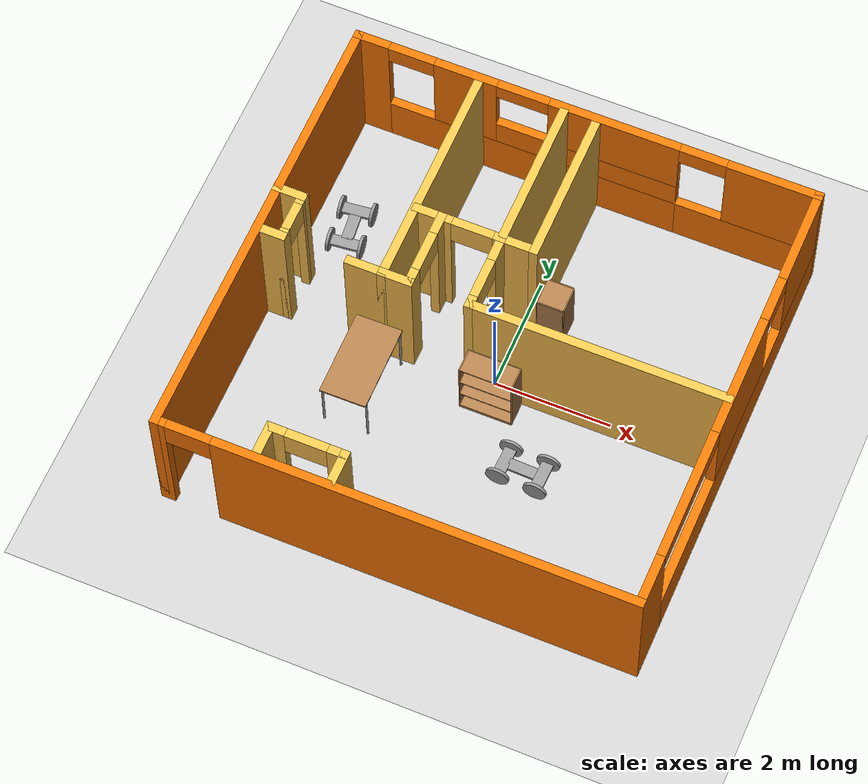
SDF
<sdf version="1.6">
 <world name="default">
  <plugin name="hello" filename="libhello.so"/>
  <light name="sun" type="directional">
   <pose>0 0 10 0 -0 0</pose>
   <diffuse>0.8 0.8 0.8 1</diffuse>
   <specular>0.2 0.2 0.2 1</specular>
   <attenuation>
    <range>1000</range>
    <constant>0.9</constant>
    <linear>0.01</linear>
    <quadratic>0.001</quadratic>
   </attenuation>
   <direction>-0.5 0.1 -0.9</direction>
  </light>
  <model name="ground_plane">
   <static>1</static>
   <link name="link">
    <collision name="collision">
     <geometry><plane><normal>0 0 1</normal><size>100 100</size></plane></geometry>
     <surface><friction><ode><mu>100</mu><mu2>50</mu2></ode></friction></surface>
    </collision>
    <visual name="visual">
     <cast_shadows>0</cast_shadows>
     <geometry><plane><normal>0 0 1</normal><size>100 100</size></plane></geometry>
     <material>
      <script><uri>file://media/materials/scripts/gazebo.material</uri><name>Gazebo/Grey</name></script>
     </material>
    </visual>
   </link>
  </model>
  <gravity>0 0 -9.8</gravity>
  <magnetic_field>6e-06 2.3e-05 -4.2e-05</magnetic_field>
  <atmosphere type="adiabatic"/>
  <physics name="default_physics" default="0" type="ode">
   <max_step_size>0.001</max_step_size>
   <real_time_factor>1</real_time_factor>
   <real_time_update_rate>1000</real_time_update_rate>
  </physics>
  <scene><ambient>0.4 0.4 0.4 1</ambient><background>0.7 0.7 0.7 1</background><shadows>1</shadows></scene>
  <spherical_coordinates>
   <surface_model>EARTH_WGS84</surface_model>
   <latitude_deg>0</latitude_deg>
   <longitude_deg>0</longitude_deg>
   <elevation>0</elevation>
   <heading_deg>0</heading_deg>
  </spherical_coordinates>
  <model name="apartment2">
   <pose>-0.038299 0.0001 0 0 -0 0</pose>
   <link name="Wall_0">
    <pose>0.0015 3.8495 0 0 -0 0</pose>
    <visual name="Wall_0_Visual_0">
     <pose>-3.74544 0 1.25 0 -0 0</pose>
     <geometry><box><size>0.63713 0.15 2.5</size></box></geometry>
     <material>
      <script><uri>file://media/materials/scripts/gazebo.material</uri><name>Gazebo/Grey</name></script>
      <ambient>0.996078 0.47451 0.0196078 1</ambient>
     </material>
     <meta><layer>0</layer></meta>
    </visual>
    <collision name="Wall_0_Collision_0">
     <geometry><box><size>0.63713 0.15 2.5</size></box></geometry>
     <pose>-3.74544 0 1.25 0 -0 0</pose>
    </collision>
    <visual name="Wall_0_Visual_1">
     <pose>-0.89256 0 0.4445 0 -0 0</pose>
     <geometry><box><size>5.06862 0.15 0.889</size></box></geometry>
     <material>
      <script><uri>file://media/materials/scripts/gazebo.material</uri><name>Gazebo/Grey</name></script>
      <ambient>0.996078 0.47451 0.0196078 1</ambient>
     </material>
     <meta><layer>0</layer></meta>
    </visual>
    <collision name="Wall_0_Collision_1">
     <geometry><box><size>5.06862 0.15 0.889</size></box></geometry>
     <pose>-0.89256 0 0.4445 0 -0 0</pose>
    </collision>
    <visual name="Wall_0_Visual_2">
     <pose>2.85288 0 0.4445 0 -0 0</pose>
     <geometry><box><size>2.42225 0.15 0.889</size></box></geometry>
     <material>
      <script><uri>file://media/materials/scripts/gazebo.material</uri><name>Gazebo/Grey</name></script>
      <ambient>0.996078 0.47451 0.0196078 1</ambient>
     </material>
     <meta><layer>0</layer></meta>
    </visual>
    <collision name="Wall_0_Collision_2">
     <geometry><box><size>2.42225 0.15 0.889</size></box></geometry>
     <pose>2.85288 0 0.4445 0 -0 0</pose>
    </collision>
    <visual name="Wall_0_Visual_3">
     <pose>3.25287 0 1.6945 0 -0 0</pose>
     <geometry><box><size>1.62225 0.15 1.611</size></box></geometry>
     <material>
      <script><uri>file://media/materials/scripts/gazebo.material</uri><name>Gazebo/Grey</name></script>
      <ambient>0.996078 0.47451 0.0196078 1</ambient>
     </material>
     <meta><layer>0</layer></meta>
    </visual>
    <collision name="Wall_0_Collision_3">
     <geometry><box><size>1.62225 0.15 1.611</size></box></geometry>
     <pose>3.25287 0 1.6945 0 -0 0</pose>
    </collision>
    <visual name="Wall_0_Visual_4">
     <pose>-2.07636 0 1.6945 0 -0 0</pose>
     <geometry><box><size>1.10102 0.15 1.611</size></box></geometry>
     <material>
      <script><uri>file://media/materials/scripts/gazebo.material</uri><name>Gazebo/Grey</name></script>
      <ambient>0.996078 0.47451 0.0196078 1</ambient>
     </material>
     <meta><layer>0</layer></meta>
    </visual>
    <collision name="Wall_0_Collision_4">
     <geometry><box><size>1.10102 0.15 1.611</size></box></geometry>
     <pose>-2.07636 0 1.6945 0 -0 0</pose>
    </collision>
    <visual name="Wall_0_Visual_5">
     <pose>-2.07636 0 1.6945 0 -0 0</pose>
     <geometry><box><size>1.10102 0.15 1.611</size></box></geometry>
     <material>
      <script><uri>file://media/materials/scripts/gazebo.material</uri><name>Gazebo/Grey</name></script>
      <ambient>0.996078 0.47451 0.0196078 1</ambient>
     </material>
     <meta><layer>0</layer></meta>
    </visual>
    <collision name="Wall_0_Collision_5">
     <geometry><box><size>1.10102 0.15 1.611</size></box></geometry>
     <pose>-2.07636 0 1.6945 0 -0 0</pose>
    </collision>
    <visual name="Wall_0_Visual_6">
     <pose>0.057948 0 1.1445 0 -0 0</pose>
     <geometry><box><size>3.1676 0.15 0.511</size></box></geometry>
     <material>
      <script><uri>file://media/materials/scripts/gazebo.material</uri><name>Gazebo/Grey</name></script>
      <ambient>0.996078 0.47451 0.0196078 1</ambient>
     </material>
     <meta><layer>0</layer></meta>
    </visual>
    <collision name="Wall_0_Collision_6">
     <geometry><box><size>3.1676 0.15 0.511</size></box></geometry>
     <pose>0.057948 0 1.1445 0 -0 0</pose>
    </collision>
    <visual name="Wall_0_Visual_7">
     <pose>0.057948 0 1.1445 0 -0 0</pose>
     <geometry><box><size>3.1676 0.15 0.511</size></box></geometry>
     <material>
      <script><uri>file://media/materials/scripts/gazebo.material</uri><name>Gazebo/Grey</name></script>
      <ambient>0.996078 0.47451 0.0196078 1</ambient>
     </material>
     <meta><layer>0</layer></meta>
    </visual>
    <collision name="Wall_0_Collision_7">
     <geometry><box><size>3.1676 0.15 0.511</size></box></geometry>
     <pose>0.057948 0 1.1445 0 -0 0</pose>
    </collision>
    <visual name="Wall_0_Visual_8">
     <pose>0.507948 0 1.95 0 -0 0</pose>
     <geometry><box><size>2.2676 0.15 1.1</size></box></geometry>
     <material>
      <script><uri>file://media/materials/scripts/gazebo.material</uri><name>Gazebo/Grey</name></script>
      <ambient>0.996078 0.47451 0.0196078 1</ambient>
     </material>
     <meta><layer>0</layer></meta>
    </visual>
    <collision name="Wall_0_Collision_8">
     <geometry><box><size>2.2676 0.15 1.1</size></box></geometry>
     <pose>0.507948 0 1.95 0 -0 0</pose>
    </collision>
    <visual name="Wall_0_Visual_9">
     <pose>0.507948 0 1.95 0 -0 0</pose>
     <geometry><box><size>2.2676 0.15 1.1</size></box></geometry>
     <material>
      <script><uri>file://media/materials/scripts/gazebo.material</uri><name>Gazebo/Grey</name></script>
      <ambient>0.996078 0.47451 0.0196078 1</ambient>
     </material>
     <meta><layer>0</layer></meta>
    </visual>
    <collision name="Wall_0_Collision_9">
     <geometry><box><size>2.2676 0.15 1.1</size></box></geometry>
     <pose>0.507948 0 1.95 0 -0 0</pose>
    </collision>
    <visual name="Wall_0_Visual_10">
     <pose>2.04175 0 2.3295 0 -0 0</pose>
     <geometry><box><size>0.8 0.15 0.341</size></box></geometry>
     <material>
      <script><uri>file://media/materials/scripts/gazebo.material</uri><name>Gazebo/Grey</name></script>
      <ambient>0.996078 0.47451 0.0196078 1</ambient>
     </material>
     <meta><layer>0</layer></meta>
    </visual>
    <collision name="Wall_0_Collision_10">
     <geometry><box><size>0.8 0.15 0.341</size></box></geometry>
     <pose>2.04175 0 2.3295 0 -0 0</pose>
    </collision>
    <visual name="Wall_0_Visual_11">
     <pose>2.04175 0 2.3295 0 -0 0</pose>
     <geometry><box><size>0.8 0.15 0.341</size></box></geometry>
     <material>
      <script><uri>file://media/materials/scripts/gazebo.material</uri><name>Gazebo/Grey</name></script>
      <ambient>0.996078 0.47451 0.0196078 1</ambient>
     </material>
     <meta><layer>0</layer></meta>
    </visual>
    <collision name="Wall_0_Collision_11">
     <geometry><box><size>0.8 0.15 0.341</size></box></geometry>
     <pose>2.04175 0 2.3295 0 -0 0</pose>
    </collision>
    <visual name="Wall_0_Visual_12">
     <pose>-3.02687 0 2.3295 0 -0 0</pose>
     <geometry><box><size>0.8 0.15 0.341</size></box></geometry>
     <material>
      <script><uri>file://media/materials/scripts/gazebo.material</uri><name>Gazebo/Grey</name></script>
      <ambient>0.996078 0.47451 0.0196078 1</ambient>
     </material>
     <meta><layer>0</layer></meta>
    </visual>
    <collision name="Wall_0_Collision_12">
     <geometry><box><size>0.8 0.15 0.341</size></box></geometry>
     <pose>-3.02687 0 2.3295 0 -0 0</pose>
    </collision>
    <visual name="Wall_0_Visual_13">
     <pose>-1.07585 0 2.35 0 -0 0</pose>
     <geometry><box><size>0.9 0.15 0.3</size></box></geometry>
     <material>
      <script><uri>file://media/materials/scripts/gazebo.material</uri><name>Gazebo/Grey</name></script>
      <ambient>0.996078 0.47451 0.0196078 1</ambient>
     </material>
     <meta><layer>0</layer></meta>
    </visual>
    <collision name="Wall_0_Collision_13">
     <geometry><box><size>0.9 0.15 0.3</size></box></geometry>
     <pose>-1.07585 0 2.35 0 -0 0</pose>
    </collision>
    <visual name="Wall_0_Visual_14">
     <pose>-1.07585 0 2.35 0 -0 0</pose>
     <geometry><box><size>0.9 0.15 0.3</size></box></geometry>
     <material>
      <script><uri>file://media/materials/scripts/gazebo.material</uri><name>Gazebo/Grey</name></script>
      <ambient>0.996078 0.47451 0.0196078 1</ambient>
     </material>
     <meta><layer>0</layer></meta>
    </visual>
    <collision name="Wall_0_Collision_14">
     <geometry><box><size>0.9 0.15 0.3</size></box></geometry>
     <pose>-1.07585 0 2.35 0 -0 0</pose>
    </collision>
   </link>
   <link name="Wall_12">
    <collision name="Wall_12_Collision">
     <geometry><box><size>4.47 0.15 2.5</size></box></geometry>
     <pose>0 0 1.25 0 -0 0</pose>
    </collision>
    <visual name="Wall_12_Visual">
     <pose>0 0 1.25 0 -0 0</pose>
     <geometry><box><size>4.47 0.15 2.5</size></box></geometry>
     <material>
      <script><uri>file://media/materials/scripts/gazebo.material</uri><name>Gazebo/Grey</name></script>
      <ambient>1 0.764706 0.305882 1</ambient>
     </material>
     <meta><layer>0</layer></meta>
    </visual>
    <pose>1.8145 -0.1125 0 0 -0 3.14159</pose>
   </link>
   <link name="Wall_14">
    <pose>-0.3455 1.8125 0 0 -0 1.5708</pose>
    <visual name="Wall_14_Visual_0">
     <pose>-1.88475 0 1.25 0 -0 0</pose>
     <geometry><box><size>0.230491 0.15 2.5</size></box></geometry>
     <material>
      <script><uri>file://media/materials/scripts/gazebo.material</uri><name>Gazebo/Grey</name></script>
      <ambient>1 0.764706 0.305882 1</ambient>
     </material>
     <meta><layer>0</layer></meta>
    </visual>
    <collision name="Wall_14_Collision_0">
     <geometry><box><size>0.230491 0.15 2.5</size></box></geometry>
     <pose>-1.88475 0 1.25 0 -0 0</pose>
    </collision>
    <visual name="Wall_14_Visual_1">
     <pose>0.470745 0 1.25 0 -0 0</pose>
     <geometry><box><size>3.05851 0.15 2.5</size></box></geometry>
     <material>
      <script><uri>file://media/materials/scripts/gazebo.material</uri><name>Gazebo/Grey</name></script>
      <ambient>1 0.764706 0.305882 1</ambient>
     </material>
     <meta><layer>0</layer></meta>
    </visual>
    <collision name="Wall_14_Collision_1">
     <geometry><box><size>3.05851 0.15 2.5</size></box></geometry>
     <pose>0.470745 0 1.25 0 -0 0</pose>
    </collision>
    <visual name="Wall_14_Visual_2">
     <pose>-1.41401 0 2.25 0 -0 0</pose>
     <geometry><box><size>0.711 0.15 0.5</size></box></geometry>
     <material>
      <script><uri>file://media/materials/scripts/gazebo.material</uri><name>Gazebo/Grey</name></script>
      <ambient>1 0.764706 0.305882 1</ambient>
     </material>
     <meta><layer>0</layer></meta>
    </visual>
    <collision name="Wall_14_Collision_2">
     <geometry><box><size>0.711 0.15 0.5</size></box></geometry>
     <pose>-1.41401 0 2.25 0 -0 0</pose>
    </collision>
   </link>
   <link name="Wall_16">
    <collision name="Wall_16_Collision">
     <geometry><box><size>4.08 0.15 2.5</size></box></geometry>
     <pose>0 0 1.25 0 -0 0</pose>
    </collision>
    <visual name="Wall_16_Visual">
     <pose>0 0 1.25 0 -0 0</pose>
     <geometry><box><size>4.08 0.15 2.5</size></box></geometry>
     <material>
      <script><uri>file://media/materials/scripts/gazebo.material</uri><name>Gazebo/Grey</name></script>
      <ambient>1 0.764706 0.305882 1</ambient>
     </material>
     <meta><layer>0</layer></meta>
    </visual>
    <pose>-1.8285 1.8525 0 0 0 -1.5708</pose>
   </link>
   <link name="Wall_18">
    <collision name="Wall_18_Collision">
     <geometry><box><size>0.711 0.15 2.5</size></box></geometry>
     <pose>0 0 1.25 0 -0 0</pose>
    </collision>
    <visual name="Wall_18_Visual">
     <pose>0 0 1.25 0 -0 0</pose>
     <geometry><box><size>0.711 0.15 2.5</size></box></geometry>
     <material>
      <script><uri>file://media/materials/scripts/gazebo.material</uri><name>Gazebo/Grey</name></script>
      <ambient>1 0.764706 0.305882 1</ambient>
     </material>
     <meta><layer>0</layer></meta>
    </visual>
    <pose>-2.109 -0.1125 0 0 -0 3.14159</pose>
   </link>
   <link name="Wall_2">
    <collision name="Wall_2_Collision">
     <geometry><box><size>7.849 0.15 2.5</size></box></geometry>
     <pose>0 0 1.25 0 -0 0</pose>
    </collision>
    <visual name="Wall_2_Visual">
     <pose>0 0 1.25 0 -0 0</pose>
     <geometry><box><size>7.849 0.15 2.5</size></box></geometry>
     <material>
      <script><uri>file://media/materials/scripts/gazebo.material</uri><name>Gazebo/Grey</name></script>
      <ambient>0.996078 0.47451 0.0196078 1</ambient>
     </material>
     <meta><layer>0</layer></meta>
    </visual>
    <pose>-3.9875 0 0 0 0 -1.5708</pose>
   </link>
   <link name="Wall_20">
    <collision name="Wall_20_Collision">
     <geometry><box><size>0.58 0.15 2.5</size></box></geometry>
     <pose>0 0 1.25 0 -0 0</pose>
    </collision>
    <visual name="Wall_20_Visual">
     <pose>0 0 1.25 0 -0 0</pose>
     <geometry><box><size>0.58 0.15 2.5</size></box></geometry>
     <material>
      <script><uri>file://media/materials/scripts/gazebo.material</uri><name>Gazebo/Grey</name></script>
      <ambient>1 0.764706 0.305882 1</ambient>
     </material>
     <meta><layer>0</layer></meta>
    </visual>
    <pose>-3.7755 -0.1125 0 0 -0 0</pose>
   </link>
   <link name="Wall_22">
    <pose>-3.5605 0.282 0 0 -0 1.5708</pose>
    <visual name="Wall_22_Visual_0">
     <pose>-0.361845 0 1.25 0 -0 0</pose>
     <geometry><box><size>0.21531 0.15 2.5</size></box></geometry>
     <material>
      <script><uri>file://media/materials/scripts/gazebo.material</uri><name>Gazebo/Grey</name></script>
      <ambient>1 0.764706 0.305882 1</ambient>
     </material>
     <meta><layer>0</layer></meta>
    </visual>
    <collision name="Wall_22_Collision_0">
     <geometry><box><size>0.21531 0.15 2.5</size></box></geometry>
     <pose>-0.361845 0 1.25 0 -0 0</pose>
    </collision>
    <visual name="Wall_22_Visual_1">
     <pose>0.357655 0 1.25 0 -0 0</pose>
     <geometry><box><size>0.22369 0.15 2.5</size></box></geometry>
     <material>
      <script><uri>file://media/materials/scripts/gazebo.material</uri><name>Gazebo/Grey</name></script>
      <ambient>1 0.764706 0.305882 1</ambient>
     </material>
     <meta><layer>0</layer></meta>
    </visual>
    <collision name="Wall_22_Collision_1">
     <geometry><box><size>0.22369 0.15 2.5</size></box></geometry>
     <pose>0.357655 0 1.25 0 -0 0</pose>
    </collision>
    <visual name="Wall_22_Visual_2">
     <pose>-0.00419 0 2.25 0 -0 0</pose>
     <geometry><box><size>0.5 0.15 0.5</size></box></geometry>
     <material>
      <script><uri>file://media/materials/scripts/gazebo.material</uri><name>Gazebo/Grey</name></script>
      <ambient>1 0.764706 0.305882 1</ambient>
     </material>
     <meta><layer>0</layer></meta>
    </visual>
    <collision name="Wall_22_Collision_2">
     <geometry><box><size>0.5 0.15 0.5</size></box></geometry>
     <pose>-0.00419 0 2.25 0 -0 0</pose>
    </collision>
   </link>
   <link name="Wall_24">
    <collision name="Wall_24_Collision">
     <geometry><box><size>0.58 0.15 2.5</size></box></geometry>
     <pose>0 0 1.25 0 -0 0</pose>
    </collision>
    <visual name="Wall_24_Visual">
     <pose>0 0 1.25 0 -0 0</pose>
     <geometry><box><size>0.58 0.15 2.5</size></box></geometry>
     <material>
      <script><uri>file://media/materials/scripts/gazebo.material</uri><name>Gazebo/Grey</name></script>
      <ambient>1 0.764706 0.305882 1</ambient>
     </material>
     <meta><layer>0</layer></meta>
    </visual>
    <pose>-3.7755 0.6765 0 0 -0 3.14159</pose>
   </link>
   <link name="Wall_26">
    <pose>-1.072 1.1825 0 0 -0 0</pose>
    <visual name="Wall_26_Visual_0">
     <pose>-0.458995 0 1.25 0 -0 0</pose>
     <geometry><box><size>0.685009 0.15 2.5</size></box></geometry>
     <material>
      <script><uri>file://media/materials/scripts/gazebo.material</uri><name>Gazebo/Grey</name></script>
      <ambient>1 0.764706 0.305882 1</ambient>
     </material>
     <meta><layer>0</layer></meta>
    </visual>
    <collision name="Wall_26_Collision_0">
     <geometry><box><size>0.685009 0.15 2.5</size></box></geometry>
     <pose>-0.458995 0 1.25 0 -0 0</pose>
    </collision>
    <visual name="Wall_26_Visual_1">
     <pose>0.698005 0 1.25 0 -0 0</pose>
     <geometry><box><size>0.206991 0.15 2.5</size></box></geometry>
     <material>
      <script><uri>file://media/materials/scripts/gazebo.material</uri><name>Gazebo/Grey</name></script>
      <ambient>1 0.764706 0.305882 1</ambient>
     </material>
     <meta><layer>0</layer></meta>
    </visual>
    <collision name="Wall_26_Collision_1">
     <geometry><box><size>0.206991 0.15 2.5</size></box></geometry>
     <pose>0.698005 0 1.25 0 -0 0</pose>
    </collision>
    <visual name="Wall_26_Visual_2">
     <pose>0.239009 0 2.25 0 -0 0</pose>
     <geometry><box><size>0.711 0.15 0.5</size></box></geometry>
     <material>
      <script><uri>file://media/materials/scripts/gazebo.material</uri><name>Gazebo/Grey</name></script>
      <ambient>1 0.764706 0.305882 1</ambient>
     </material>
     <meta><layer>0</layer></meta>
    </visual>
    <collision name="Wall_26_Collision_2">
     <geometry><box><size>0.711 0.15 0.5</size></box></geometry>
     <pose>0.239009 0 2.25 0 -0 0</pose>
    </collision>
   </link>
   <link name="Wall_39">
    <collision name="Wall_39_Collision">
     <geometry><box><size>0.711 0.15 2.5</size></box></geometry>
     <pose>0 0 1.25 0 -0 0</pose>
    </collision>
    <visual name="Wall_39_Visual">
     <pose>0 0 1.25 0 -0 0</pose>
     <geometry><box><size>0.711 0.15 2.5</size></box></geometry>
     <material>
      <script><uri>file://media/materials/scripts/gazebo.material</uri><name>Gazebo/Grey</name></script>
      <ambient>1 0.764706 0.305882 1</ambient>
     </material>
     <meta><layer>0</layer></meta>
    </visual>
    <pose>-0.065 1.1825 0 0 -0 0</pose>
   </link>
   <link name="Wall_4">
    <pose>0.0015 -3.8495 0 0 -0 0</pose>
    <visual name="Wall_4_Visual_0">
     <pose>-3.93707 0 1.25 0 -0 0</pose>
     <geometry><box><size>0.253859 0.15 2.5</size></box></geometry>
     <material>
      <script><uri>file://media/materials/scripts/gazebo.material</uri><name>Gazebo/Grey</name></script>
      <ambient>0.996078 0.47451 0.0196078 1</ambient>
     </material>
     <meta><layer>0</layer></meta>
    </visual>
    <collision name="Wall_4_Collision_0">
     <geometry><box><size>0.253859 0.15 2.5</size></box></geometry>
     <pose>-3.93707 0 1.25 0 -0 0</pose>
    </collision>
    <visual name="Wall_4_Visual_1">
     <pose>0.507929 0 1.25 0 -0 0</pose>
     <geometry><box><size>7.11214 0.15 2.5</size></box></geometry>
     <material>
      <script><uri>file://media/materials/scripts/gazebo.material</uri><name>Gazebo/Grey</name></script>
      <ambient>0.996078 0.47451 0.0196078 1</ambient>
     </material>
     <meta><layer>0</layer></meta>
    </visual>
    <collision name="Wall_4_Collision_1">
     <geometry><box><size>7.11214 0.15 2.5</size></box></geometry>
     <pose>0.507929 0 1.25 0 -0 0</pose>
    </collision>
    <visual name="Wall_4_Visual_2">
     <pose>-3.42914 0 2.25 0 -0 0</pose>
     <geometry><box><size>0.762 0.15 0.5</size></box></geometry>
     <material>
      <script><uri>file://media/materials/scripts/gazebo.material</uri><name>Gazebo/Grey</name></script>
      <ambient>0.996078 0.47451 0.0196078 1</ambient>
     </material>
     <meta><layer>0</layer></meta>
    </visual>
    <collision name="Wall_4_Collision_2">
     <geometry><box><size>0.762 0.15 0.5</size></box></geometry>
     <pose>-3.42914 0 2.25 0 -0 0</pose>
    </collision>
   </link>
   <link name="Wall_41">
    <collision name="Wall_41_Collision">
     <geometry><box><size>2.817 0.15 2.5</size></box></geometry>
     <pose>0 0 1.25 0 -0 0</pose>
    </collision>
    <visual name="Wall_41_Visual">
     <pose>0 0 1.25 0 -0 0</pose>
     <geometry><box><size>2.817 0.15 2.5</size></box></geometry>
     <material>
      <script><uri>file://media/materials/scripts/gazebo.material</uri><name>Gazebo/Grey</name></script>
      <ambient>1 0.764706 0.305882 1</ambient>
     </material>
     <meta><layer>0</layer></meta>
    </visual>
    <pose>0.2155 2.516 0 0 -0 1.5708</pose>
   </link>
   <link name="Wall_43">
    <collision name="Wall_43_Collision">
     <geometry><box><size>0.6 0.15 2.5</size></box></geometry>
     <pose>0 0 1.25 0 -0 0</pose>
    </collision>
    <visual name="Wall_43_Visual">
     <pose>0 0 1.25 0 -0 0</pose>
     <geometry><box><size>0.6 0.15 2.5</size></box></geometry>
     <material>
      <script><uri>file://media/materials/scripts/gazebo.material</uri><name>Gazebo/Grey</name></script>
      <ambient>1 0.764706 0.305882 1</ambient>
     </material>
     <meta><layer>0</layer></meta>
    </visual>
    <pose>-1.6035 -0.1125 0 0 -0 0</pose>
   </link>
   <link name="Wall_46">
    <pose>-1.3785 0.535 0 0 -0 1.5708</pose>
    <visual name="Wall_46_Visual_0">
     <pose>-0.556971 0 1.25 0 -0 0</pose>
     <geometry><box><size>0.331058 0.15 2.5</size></box></geometry>
     <material>
      <script><uri>file://media/materials/scripts/gazebo.material</uri><name>Gazebo/Grey</name></script>
      <ambient>1 0.764706 0.305882 1</ambient>
     </material>
     <meta><layer>0</layer></meta>
    </visual>
    <collision name="Wall_46_Collision_0">
     <geometry><box><size>0.331058 0.15 2.5</size></box></geometry>
     <pose>-0.556971 0 1.25 0 -0 0</pose>
    </collision>
    <visual name="Wall_46_Visual_1">
     <pose>0.521029 0 1.25 0 -0 0</pose>
     <geometry><box><size>0.402942 0.15 2.5</size></box></geometry>
     <material>
      <script><uri>file://media/materials/scripts/gazebo.material</uri><name>Gazebo/Grey</name></script>
      <ambient>1 0.764706 0.305882 1</ambient>
     </material>
     <meta><layer>0</layer></meta>
    </visual>
    <collision name="Wall_46_Collision_1">
     <geometry><box><size>0.402942 0.15 2.5</size></box></geometry>
     <pose>0.521029 0 1.25 0 -0 0</pose>
    </collision>
    <visual name="Wall_46_Visual_2">
     <pose>-0.035942 0 2.25 0 -0 0</pose>
     <geometry><box><size>0.711 0.15 0.5</size></box></geometry>
     <material>
      <script><uri>file://media/materials/scripts/gazebo.material</uri><name>Gazebo/Grey</name></script>
      <ambient>1 0.764706 0.305882 1</ambient>
     </material>
     <meta><layer>0</layer></meta>
    </visual>
    <collision name="Wall_46_Collision_2">
     <geometry><box><size>0.711 0.15 0.5</size></box></geometry>
     <pose>-0.035942 0 2.25 0 -0 0</pose>
    </collision>
   </link>
   <link name="Wall_51">
    <collision name="Wall_51_Collision">
     <geometry><box><size>0.711 0.15 2.5</size></box></geometry>
     <pose>0 0 1.25 0 -0 0</pose>
    </collision>
    <visual name="Wall_51_Visual">
     <pose>0 0 1.25 0 -0 0</pose>
     <geometry><box><size>0.711 0.15 2.5</size></box></geometry>
     <material>
      <script><uri>file://media/materials/scripts/gazebo.material</uri><name>Gazebo/Grey</name></script>
      <ambient>1 0.764706 0.305882 1</ambient>
     </material>
     <meta><layer>0</layer></meta>
    </visual>
    <pose>-2.3175 -3.565 0 0 -0 1.5708</pose>
   </link>
   <link name="Wall_53">
    <pose>-1.694 -3.2845 0 0 -0 0</pose>
    <visual name="Wall_53_Visual_0">
     <pose>-0.528937 0 1.25 0 -0 0</pose>
     <geometry><box><size>0.339126 0.15 2.5</size></box></geometry>
     <material>
      <script><uri>file://media/materials/scripts/gazebo.material</uri><name>Gazebo/Grey</name></script>
      <ambient>1 0.764706 0.305882 1</ambient>
     </material>
     <meta><layer>0</layer></meta>
    </visual>
    <collision name="Wall_53_Collision_0">
     <geometry><box><size>0.339126 0.15 2.5</size></box></geometry>
     <pose>-0.528937 0 1.25 0 -0 0</pose>
    </collision>
    <visual name="Wall_53_Visual_1">
     <pose>0.525063 0 1.25 0 -0 0</pose>
     <geometry><box><size>0.346874 0.15 2.5</size></box></geometry>
     <material>
      <script><uri>file://media/materials/scripts/gazebo.material</uri><name>Gazebo/Grey</name></script>
      <ambient>1 0.764706 0.305882 1</ambient>
     </material>
     <meta><layer>0</layer></meta>
    </visual>
    <collision name="Wall_53_Collision_1">
     <geometry><box><size>0.346874 0.15 2.5</size></box></geometry>
     <pose>0.525063 0 1.25 0 -0 0</pose>
    </collision>
    <visual name="Wall_53_Visual_2">
     <pose>-0.003874 0 2.25 0 -0 0</pose>
     <geometry><box><size>0.711 0.15 0.5</size></box></geometry>
     <material>
      <script><uri>file://media/materials/scripts/gazebo.material</uri><name>Gazebo/Grey</name></script>
      <ambient>1 0.764706 0.305882 1</ambient>
     </material>
     <meta><layer>0</layer></meta>
    </visual>
    <collision name="Wall_53_Collision_2">
     <geometry><box><size>0.711 0.15 0.5</size></box></geometry>
     <pose>-0.003874 0 2.25 0 -0 0</pose>
    </collision>
   </link>
   <link name="Wall_57">
    <collision name="Wall_57_Collision">
     <geometry><box><size>0.711 0.15 2.5</size></box></geometry>
     <pose>0 0 1.25 0 -0 0</pose>
    </collision>
    <visual name="Wall_57_Visual">
     <pose>0 0 1.25 0 -0 0</pose>
     <geometry><box><size>0.711 0.15 2.5</size></box></geometry>
     <material>
      <script><uri>file://media/materials/scripts/gazebo.material</uri><name>Gazebo/Grey</name></script>
      <ambient>1 0.764706 0.305882 1</ambient>
     </material>
     <meta><layer>0</layer></meta>
    </visual>
    <pose>-1.0705 -3.565 0 0 0 -1.5708</pose>
   </link>
   <link name="Wall_8">
    <pose>3.9905 0 0 0 -0 1.5708</pose>
    <visual name="Wall_8_Visual_0">
     <pose>-3.46767 0 1.25 0 -0 0</pose>
     <geometry><box><size>0.913657 0.15 2.5</size></box></geometry>
     <material>
      <script><uri>file://media/materials/scripts/gazebo.material</uri><name>Gazebo/Grey</name></script>
      <ambient>0.996078 0.47451 0.0196078 1</ambient>
     </material>
     <meta><layer>0</layer></meta>
    </visual>
    <collision name="Wall_8_Collision_0">
     <geometry><box><size>0.913657 0.15 2.5</size></box></geometry>
     <pose>-3.46767 0 1.25 0 -0 0</pose>
    </collision>
    <visual name="Wall_8_Visual_1">
     <pose>0.456829 0 0.4445 0 -0 0</pose>
     <geometry><box><size>6.93534 0.15 0.889</size></box></geometry>
     <material>
      <script><uri>file://media/materials/scripts/gazebo.material</uri><name>Gazebo/Grey</name></script>
      <ambient>0.996078 0.47451 0.0196078 1</ambient>
     </material>
     <meta><layer>0</layer></meta>
    </visual>
    <collision name="Wall_8_Collision_1">
     <geometry><box><size>6.93534 0.15 0.889</size></box></geometry>
     <pose>0.456829 0 0.4445 0 -0 0</pose>
    </collision>
    <visual name="Wall_8_Visual_2">
     <pose>0.334299 0 1.6945 0 -0 0</pose>
     <geometry><box><size>2.14428 0.15 1.611</size></box></geometry>
     <material>
      <script><uri>file://media/materials/scripts/gazebo.material</uri><name>Gazebo/Grey</name></script>
      <ambient>0.996078 0.47451 0.0196078 1</ambient>
     </material>
     <meta><layer>0</layer></meta>
    </visual>
    <collision name="Wall_8_Collision_2">
     <geometry><box><size>2.14428 0.15 1.611</size></box></geometry>
     <pose>0.334299 0 1.6945 0 -0 0</pose>
    </collision>
    <visual name="Wall_8_Visual_3">
     <pose>3.06547 0 1.6945 0 -0 0</pose>
     <geometry><box><size>1.71806 0.15 1.611</size></box></geometry>
     <material>
      <script><uri>file://media/materials/scripts/gazebo.material</uri><name>Gazebo/Grey</name></script>
      <ambient>0.996078 0.47451 0.0196078 1</ambient>
     </material>
     <meta><layer>0</layer></meta>
    </visual>
    <collision name="Wall_8_Collision_3">
     <geometry><box><size>1.71806 0.15 1.611</size></box></geometry>
     <pose>3.06547 0 1.6945 0 -0 0</pose>
    </collision>
    <visual name="Wall_8_Visual_4">
     <pose>-1.87434 0 2.3295 0 -0 0</pose>
     <geometry><box><size>2.273 0.15 0.341</size></box></geometry>
     <material>
      <script><uri>file://media/materials/scripts/gazebo.material</uri><name>Gazebo/Grey</name></script>
      <ambient>0.996078 0.47451 0.0196078 1</ambient>
     </material>
     <meta><layer>0</layer></meta>
    </visual>
    <collision name="Wall_8_Collision_4">
     <geometry><box><size>2.273 0.15 0.341</size></box></geometry>
     <pose>-1.87434 0 2.3295 0 -0 0</pose>
    </collision>
    <visual name="Wall_8_Visual_5">
     <pose>1.80644 0 2.3295 0 -0 0</pose>
     <geometry><box><size>0.8 0.15 0.341</size></box></geometry>
     <material>
      <script><uri>file://media/materials/scripts/gazebo.material</uri><name>Gazebo/Grey</name></script>
      <ambient>0.996078 0.47451 0.0196078 1</ambient>
     </material>
     <meta><layer>0</layer></meta>
    </visual>
    <collision name="Wall_8_Collision_5">
     <geometry><box><size>0.8 0.15 0.341</size></box></geometry>
     <pose>1.80644 0 2.3295 0 -0 0</pose>
    </collision>
   </link>
   <static>1</static>
  </model>
  <model name="rccar-no-friction">
   <link name="link_0">
    <pose>-0 0 0.2 0 -0 0</pose>
    <inertial>
     <mass>1</mass>
     <inertia>
      <ixx>0.166667</ixx>
      <ixy>0</ixy>
      <ixz>0</ixz>
      <iyy>0.166667</iyy>
      <iyz>0</iyz>
      <izz>0.166667</izz>
     </inertia>
    </inertial>
    <visual name="visual">
     <geometry><box><size>0.5 0.2 0.05</size></box></geometry>
     <material>
      <lighting>1</lighting>
      <script><uri>file://media/materials/scripts/gazebo.material</uri><name>Gazebo/Grey</name></script>
      <ambient>0.3 0.3 0.3 1</ambient>
      <diffuse>0.7 0.7 0.7 1</diffuse>
      <specular>0.01 0.01 0.01 1</specular>
      <emissive>0 0 0 1</emissive>
      <shader type="vertex"><normal_map>__default__</normal_map></shader>
     </material>
    </visual>
    <collision name="collision">
     <geometry><box><size>0.5 0.2 0.05</size></box></geometry>
     <surface>
      <friction>
       <ode><mu>1</mu><mu2>1</mu2><fdir1>0 0 0</fdir1><slip1>0</slip1><slip2>0</slip2></ode>
       <torsional>
        <coefficient>1</coefficient>
        <patch_radius>0</patch_radius>
        <surface_radius>0</surface_radius>
        <use_patch_radius>1</use_patch_radius>
        <ode><slip>0</slip></ode>
       </torsional>
      </friction>
      <bounce><restitution_coefficient>0</restitution_coefficient><threshold>1e+06</threshold></bounce>
      <contact>
       <collide_without_contact>0</collide_without_contact>
       <collide_without_contact_bitmask>1</collide_without_contact_bitmask>
       <collide_bitmask>1</collide_bitmask>
       <ode>
        <soft_cfm>0</soft_cfm>
        <soft_erp>0.2</soft_erp>
        <kp>1e+13</kp>
        <kd>1</kd>
        <max_vel>0.01</max_vel>
        <min_depth>0</min_depth>
       </ode>
       <bullet>
        <split_impulse>1</split_impulse>
        <split_impulse_penetration_threshold>-0.01</split_impulse_penetration_threshold>
        <soft_cfm>0</soft_cfm>
        <soft_erp>0.2</soft_erp>
        <kp>1e+13</kp>
        <kd>1</kd>
       </bullet>
      </contact>
     </surface>
    </collision>
   </link>
   <link name="link_0_0">
    <pose>-0 -0.322937 0.2 0 -0 0</pose>
    <inertial>
     <mass>1</mass>
     <inertia>
      <ixx>0.166667</ixx>
      <ixy>0</ixy>
      <ixz>0</ixz>
      <iyy>0.166667</iyy>
      <iyz>0</iyz>
      <izz>0.166667</izz>
     </inertia>
    </inertial>
    <visual name="visual">
     <geometry><box><size>0.2 0.5 0.05</size></box></geometry>
     <material>
      <lighting>1</lighting>
      <script><uri>file://media/materials/scripts/gazebo.material</uri><name>Gazebo/Grey</name></script>
      <ambient>0.3 0.3 0.3 1</ambient>
      <diffuse>0.7 0.7 0.7 1</diffuse>
      <specular>0.01 0.01 0.01 1</specular>
      <emissive>0 0 0 1</emissive>
      <shader type="vertex"><normal_map>__default__</normal_map></shader>
     </material>
    </visual>
    <collision name="collision">
     <geometry><box><size>0.2 0.5 0.05</size></box></geometry>
     <surface>
      <friction>
       <ode><mu>1</mu><mu2>1</mu2><fdir1>0 0 0</fdir1><slip1>0</slip1><slip2>0</slip2></ode>
       <torsional>
        <coefficient>1</coefficient>
        <patch_radius>0</patch_radius>
        <surface_radius>0</surface_radius>
        <use_patch_radius>1</use_patch_radius>
        <ode><slip>0</slip></ode>
       </torsional>
      </friction>
      <bounce><restitution_coefficient>0</restitution_coefficient><threshold>1e+06</threshold></bounce>
      <contact>
       <collide_without_contact>0</collide_without_contact>
       <collide_without_contact_bitmask>1</collide_without_contact_bitmask>
       <collide_bitmask>1</collide_bitmask>
       <ode>
        <soft_cfm>0</soft_cfm>
        <soft_erp>0.2</soft_erp>
        <kp>1e+13</kp>
        <kd>1</kd>
        <max_vel>0.01</max_vel>
        <min_depth>0</min_depth>
       </ode>
       <bullet>
        <split_impulse>1</split_impulse>
        <split_impulse_penetration_threshold>-0.01</split_impulse_penetration_threshold>
        <soft_cfm>0</soft_cfm>
        <soft_erp>0.2</soft_erp>
        <kp>1e+13</kp>
        <kd>1</kd>
       </bullet>
      </contact>
     </surface>
    </collision>
   </link>
   <link name="link_0_clone">
    <pose>0.002934 -0.646886 0.2 0 -0 0</pose>
    <inertial>
     <mass>1</mass>
     <inertia>
      <ixx>0.166667</ixx>
      <ixy>0</ixy>
      <ixz>0</ixz>
      <iyy>0.166667</iyy>
      <iyz>0</iyz>
      <izz>0.166667</izz>
     </inertia>
    </inertial>
    <visual name="visual">
     <geometry><box><size>0.5 0.2 0.05</size></box></geometry>
     <material>
      <lighting>1</lighting>
      <script><uri>file://media/materials/scripts/gazebo.material</uri><name>Gazebo/Grey</name></script>
      <ambient>0.3 0.3 0.3 1</ambient>
      <diffuse>0.7 0.7 0.7 1</diffuse>
      <specular>0.01 0.01 0.01 1</specular>
      <emissive>0 0 0 1</emissive>
      <shader type="vertex"><normal_map>__default__</normal_map></shader>
     </material>
    </visual>
    <collision name="collision">
     <geometry><box><size>0.5 0.2 0.05</size></box></geometry>
     <surface>
      <friction>
       <ode><mu>1</mu><mu2>1</mu2><fdir1>0 0 0</fdir1><slip1>0</slip1><slip2>0</slip2></ode>
       <torsional>
        <coefficient>1</coefficient>
        <patch_radius>0</patch_radius>
        <surface_radius>0</surface_radius>
        <use_patch_radius>1</use_patch_radius>
        <ode><slip>0</slip></ode>
       </torsional>
      </friction>
      <bounce><restitution_coefficient>0</restitution_coefficient><threshold>1e+06</threshold></bounce>
      <contact>
       <collide_without_contact>0</collide_without_contact>
       <collide_without_contact_bitmask>1</collide_without_contact_bitmask>
       <collide_bitmask>1</collide_bitmask>
       <ode>
        <soft_cfm>0</soft_cfm>
        <soft_erp>0.2</soft_erp>
        <kp>1e+13</kp>
        <kd>1</kd>
        <max_vel>0.01</max_vel>
        <min_depth>0</min_depth>
       </ode>
       <bullet>
        <split_impulse>1</split_impulse>
        <split_impulse_penetration_threshold>-0.01</split_impulse_penetration_threshold>
        <soft_cfm>0</soft_cfm>
        <soft_erp>0.2</soft_erp>
        <kp>1e+13</kp>
        <kd>1</kd>
       </bullet>
      </contact>
     </surface>
    </collision>
   </link>
   <link name="link_1">
    <pose>0.275001 -0 0.2 1.5708 -0 1.5708</pose>
    <inertial>
     <mass>1</mass>
     <inertia><ixx>0.145833</ixx><ixy>0</ixy><ixz>0</ixz><iyy>0.145833</iyy><iyz>0</iyz><izz>0.125</izz></inertia>
    </inertial>
    <visual name="visual">
     <geometry><cylinder><radius>0.2</radius><length>0.05</length></cylinder></geometry>
     <material>
      <lighting>1</lighting>
      <script><uri>file://media/materials/scripts/gazebo.material</uri><name>Gazebo/Grey</name></script>
      <ambient>0.3 0.3 0.3 1</ambient>
      <diffuse>0.7 0.7 0.7 1</diffuse>
      <specular>0.01 0.01 0.01 1</specular>
      <emissive>0 0 0 1</emissive>
      <shader type="vertex"><normal_map>__default__</normal_map></shader>
     </material>
    </visual>
    <collision name="collision">
     <geometry><cylinder><radius>0.2</radius><length>0.05</length></cylinder></geometry>
     <surface>
      <friction>
       <ode><mu>1</mu><mu2>1</mu2><fdir1>0 0 0</fdir1><slip1>0</slip1><slip2>0</slip2></ode>
       <torsional>
        <coefficient>1</coefficient>
        <patch_radius>0</patch_radius>
        <surface_radius>0</surface_radius>
        <use_patch_radius>1</use_patch_radius>
        <ode><slip>0</slip></ode>
       </torsional>
      </friction>
      <bounce><restitution_coefficient>0</restitution_coefficient><threshold>1e+06</threshold></bounce>
      <contact>
       <collide_without_contact>0</collide_without_contact>
       <collide_without_contact_bitmask>1</collide_without_contact_bitmask>
       <collide_bitmask>1</collide_bitmask>
       <ode>
        <soft_cfm>0</soft_cfm>
        <soft_erp>0.2</soft_erp>
        <kp>1e+13</kp>
        <kd>1</kd>
        <max_vel>0.01</max_vel>
        <min_depth>0</min_depth>
       </ode>
       <bullet>
        <split_impulse>1</split_impulse>
        <split_impulse_penetration_threshold>-0.01</split_impulse_penetration_threshold>
        <soft_cfm>0</soft_cfm>
        <soft_erp>0.2</soft_erp>
        <kp>1e+13</kp>
        <kd>1</kd>
       </bullet>
      </contact>
     </surface>
    </collision>
   </link>
   <link name="link_1_clone">
    <pose>-0.275001 0 0.2 -1.5708 0 1.5708</pose>
    <inertial>
     <mass>1</mass>
     <inertia><ixx>0.145833</ixx><ixy>0</ixy><ixz>0</ixz><iyy>0.145833</iyy><iyz>0</iyz><izz>0.125</izz></inertia>
    </inertial>
    <visual name="visual">
     <geometry><cylinder><radius>0.2</radius><length>0.05</length></cylinder></geometry>
     <material>
      <lighting>1</lighting>
      <script><uri>file://media/materials/scripts/gazebo.material</uri><name>Gazebo/Grey</name></script>
      <ambient>0.3 0.3 0.3 1</ambient>
      <diffuse>0.7 0.7 0.7 1</diffuse>
      <specular>0.01 0.01 0.01 1</specular>
      <emissive>0 0 0 1</emissive>
      <shader type="vertex"><normal_map>__default__</normal_map></shader>
     </material>
    </visual>
    <collision name="collision">
     <geometry><cylinder><radius>0.2</radius><length>0.05</length></cylinder></geometry>
     <surface>
      <friction>
       <ode><mu>1</mu><mu2>1</mu2><fdir1>0 0 0</fdir1><slip1>0</slip1><slip2>0</slip2></ode>
       <torsional>
        <coefficient>1</coefficient>
        <patch_radius>0</patch_radius>
        <surface_radius>0</surface_radius>
        <use_patch_radius>1</use_patch_radius>
        <ode><slip>0</slip></ode>
       </torsional>
      </friction>
      <bounce><restitution_coefficient>0</restitution_coefficient><threshold>1e+06</threshold></bounce>
      <contact>
       <collide_without_contact>0</collide_without_contact>
       <collide_without_contact_bitmask>1</collide_without_contact_bitmask>
       <collide_bitmask>1</collide_bitmask>
       <ode>
        <soft_cfm>0</soft_cfm>
        <soft_erp>0.2</soft_erp>
        <kp>1e+13</kp>
        <kd>1</kd>
        <max_vel>0.01</max_vel>
        <min_depth>0</min_depth>
       </ode>
       <bullet>
        <split_impulse>1</split_impulse>
        <split_impulse_penetration_threshold>-0.01</split_impulse_penetration_threshold>
        <soft_cfm>0</soft_cfm>
        <soft_erp>0.2</soft_erp>
        <kp>1e+13</kp>
        <kd>1</kd>
       </bullet>
      </contact>
     </surface>
    </collision>
   </link>
   <link name="link_1_clone_clone">
    <pose>-0.272068 -0.646886 0.2 -1.5708 0 1.5708</pose>
    <inertial>
     <mass>1</mass>
     <inertia><ixx>0.145833</ixx><ixy>0</ixy><ixz>0</ixz><iyy>0.145833</iyy><iyz>0</iyz><izz>0.125</izz></inertia>
    </inertial>
    <visual name="visual">
     <geometry><cylinder><radius>0.2</radius><length>0.05</length></cylinder></geometry>
     <material>
      <lighting>1</lighting>
      <script><uri>file://media/materials/scripts/gazebo.material</uri><name>Gazebo/Grey</name></script>
      <ambient>0.3 0.3 0.3 1</ambient>
      <diffuse>0.7 0.7 0.7 1</diffuse>
      <specular>0.01 0.01 0.01 1</specular>
      <emissive>0 0 0 1</emissive>
      <shader type="vertex"><normal_map>__default__</normal_map></shader>
     </material>
    </visual>
    <collision name="collision">
     <geometry><cylinder><radius>0.2</radius><length>0.05</length></cylinder></geometry>
     <surface>
      <friction>
       <ode><mu>1</mu><mu2>1</mu2><fdir1>0 0 0</fdir1><slip1>0</slip1><slip2>0</slip2></ode>
       <torsional>
        <coefficient>1</coefficient>
        <patch_radius>0</patch_radius>
        <surface_radius>0</surface_radius>
        <use_patch_radius>1</use_patch_radius>
        <ode><slip>0</slip></ode>
       </torsional>
      </friction>
      <bounce><restitution_coefficient>0</restitution_coefficient><threshold>1e+06</threshold></bounce>
      <contact>
       <collide_without_contact>0</collide_without_contact>
       <collide_without_contact_bitmask>1</collide_without_contact_bitmask>
       <collide_bitmask>1</collide_bitmask>
       <ode>
        <soft_cfm>0</soft_cfm>
        <soft_erp>0.2</soft_erp>
        <kp>1e+13</kp>
        <kd>1</kd>
        <max_vel>0.01</max_vel>
        <min_depth>0</min_depth>
       </ode>
       <bullet>
        <split_impulse>1</split_impulse>
        <split_impulse_penetration_threshold>-0.01</split_impulse_penetration_threshold>
        <soft_cfm>0</soft_cfm>
        <soft_erp>0.2</soft_erp>
        <kp>1e+13</kp>
        <kd>1</kd>
       </bullet>
      </contact>
     </surface>
    </collision>
   </link>
   <link name="link_1_clone_clone_0">
    <pose>0.277936 -0.646886 0.2 -1.5708 0 1.5708</pose>
    <inertial>
     <mass>1</mass>
     <inertia><ixx>0.145833</ixx><ixy>0</ixy><ixz>0</ixz><iyy>0.145833</iyy><iyz>0</iyz><izz>0.125</izz></inertia>
    </inertial>
    <visual name="visual">
     <geometry><cylinder><radius>0.2</radius><length>0.05</length></cylinder></geometry>
     <material>
      <lighting>1</lighting>
      <script><uri>file://media/materials/scripts/gazebo.material</uri><name>Gazebo/Grey</name></script>
      <ambient>0.3 0.3 0.3 1</ambient>
      <diffuse>0.7 0.7 0.7 1</diffuse>
      <specular>0.01 0.01 0.01 1</specular>
      <emissive>0 0 0 1</emissive>
      <shader type="vertex"><normal_map>__default__</normal_map></shader>
     </material>
    </visual>
    <collision name="collision">
     <geometry><cylinder><radius>0.2</radius><length>0.05</length></cylinder></geometry>
     <surface>
      <friction>
       <ode><mu>1</mu><mu2>1</mu2><fdir1>0 0 0</fdir1><slip1>0</slip1><slip2>0</slip2></ode>
       <torsional>
        <coefficient>1</coefficient>
        <patch_radius>0</patch_radius>
        <surface_radius>0</surface_radius>
        <use_patch_radius>1</use_patch_radius>
        <ode><slip>0</slip></ode>
       </torsional>
      </friction>
      <bounce><restitution_coefficient>0</restitution_coefficient><threshold>1e+06</threshold></bounce>
      <contact>
       <collide_without_contact>0</collide_without_contact>
       <collide_without_contact_bitmask>1</collide_without_contact_bitmask>
       <collide_bitmask>1</collide_bitmask>
       <ode>
        <soft_cfm>0</soft_cfm>
        <soft_erp>0.2</soft_erp>
        <kp>1e+13</kp>
        <kd>1</kd>
        <max_vel>0.01</max_vel>
        <min_depth>0</min_depth>
       </ode>
       <bullet>
        <split_impulse>1</split_impulse>
        <split_impulse_penetration_threshold>-0.01</split_impulse_penetration_threshold>
        <soft_cfm>0</soft_cfm>
        <soft_erp>0.2</soft_erp>
        <kp>1e+13</kp>
        <kd>1</kd>
       </bullet>
      </contact>
     </surface>
    </collision>
   </link>
   <joint name="link_0_0_JOINT_2" type="fixed">
    <parent>link_0</parent>
    <child>link_0_0</child>
    <physics>
     <ode><limit><cfm>0</cfm><erp>0.2</erp></limit><suspension><cfm>0</cfm><erp>0.2</erp></suspension></ode>
    </physics>
   </joint>
   <joint name="link_0_0_JOINT_3" type="fixed">
    <parent>link_0_0</parent>
    <child>link_0_clone</child>
    <physics>
     <ode><limit><cfm>0</cfm><erp>0.2</erp></limit><suspension><cfm>0</cfm><erp>0.2</erp></suspension></ode>
    </physics>
   </joint>
   <joint name="link_0_JOINT_0" type="revolute">
    <parent>link_0</parent>
    <child>link_1</child>
    <axis>
     <xyz>0 0 1</xyz>
     <use_parent_model_frame>0</use_parent_model_frame>
     <limit>
      <lower>-1.79769e+308</lower>
      <upper>1.79769e+308</upper>
      <effort>-1</effort>
      <velocity>-1</velocity>
     </limit>
     <dynamics>
      <spring_reference>0</spring_reference>
      <spring_stiffness>0</spring_stiffness>
      <damping>0</damping>
      <friction>0</friction>
     </dynamics>
    </axis>
    <physics>
     <ode><limit><cfm>0</cfm><erp>0.2</erp></limit><suspension><cfm>0</cfm><erp>0.2</erp></suspension></ode>
    </physics>
   </joint>
   <joint name="link_0_JOINT_2" type="revolute">
    <parent>link_0</parent>
    <child>link_1_clone</child>
    <axis>
     <xyz>0 0 1</xyz>
     <use_parent_model_frame>0</use_parent_model_frame>
     <limit>
      <lower>-1.79769e+308</lower>
      <upper>1.79769e+308</upper>
      <effort>-1</effort>
      <velocity>-1</velocity>
     </limit>
     <dynamics>
      <spring_reference>0</spring_reference>
      <spring_stiffness>0</spring_stiffness>
      <damping>0</damping>
      <friction>0</friction>
     </dynamics>
    </axis>
    <physics>
     <ode><limit><cfm>0</cfm><erp>0.2</erp></limit><suspension><cfm>0</cfm><erp>0.2</erp></suspension></ode>
    </physics>
   </joint>
   <joint name="link_0_clone_JOINT_4" type="revolute">
    <parent>link_0_clone</parent>
    <child>link_1_clone_clone</child>
    <axis>
     <xyz>0 0 1</xyz>
     <use_parent_model_frame>0</use_parent_model_frame>
     <limit>
      <lower>-1.79769e+308</lower>
      <upper>1.79769e+308</upper>
      <effort>-1</effort>
      <velocity>-1</velocity>
     </limit>
     <dynamics>
      <spring_reference>0</spring_reference>
      <spring_stiffness>0</spring_stiffness>
      <damping>0</damping>
      <friction>0</friction>
     </dynamics>
    </axis>
    <physics>
     <ode><limit><cfm>0</cfm><erp>0.2</erp></limit><suspension><cfm>0</cfm><erp>0.2</erp></suspension></ode>
    </physics>
   </joint>
   <joint name="link_0_clone_JOINT_5" type="revolute">
    <parent>link_0_clone</parent>
    <child>link_1_clone_clone_0</child>
    <axis>
     <xyz>0 0 -1</xyz>
     <use_parent_model_frame>0</use_parent_model_frame>
     <limit>
      <lower>-1.79769e+308</lower>
      <upper>1.79769e+308</upper>
      <effort>-1</effort>
      <velocity>-1</velocity>
     </limit>
     <dynamics>
      <spring_reference>0</spring_reference>
      <spring_stiffness>0</spring_stiffness>
      <damping>0</damping>
      <friction>0</friction>
     </dynamics>
    </axis>
    <physics>
     <ode><limit><cfm>0</cfm><erp>0.2</erp></limit><suspension><cfm>0</cfm><erp>0.2</erp></suspension></ode>
    </physics>
   </joint>
   <static>0</static>
   <pose>-3.32004 2.022 -1e-06 -0 3e-06 0.108027</pose>
  </model>
  <model name="rccar-no-friction_clone">
   <link name="link_0">
    <pose>-0 0 0.2 0 -0 0</pose>
    <inertial>
     <mass>1</mass>
     <inertia>
      <ixx>0.166667</ixx>
      <ixy>0</ixy>
      <ixz>0</ixz>
      <iyy>0.166667</iyy>
      <iyz>0</iyz>
      <izz>0.166667</izz>
     </inertia>
    </inertial>
    <visual name="visual">
     <geometry><box><size>0.5 0.2 0.05</size></box></geometry>
     <material>
      <lighting>1</lighting>
      <script><uri>file://media/materials/scripts/gazebo.material</uri><name>Gazebo/Grey</name></script>
      <ambient>0.3 0.3 0.3 1</ambient>
      <diffuse>0.7 0.7 0.7 1</diffuse>
      <specular>0.01 0.01 0.01 1</specular>
      <emissive>0 0 0 1</emissive>
      <shader type="vertex"><normal_map>__default__</normal_map></shader>
     </material>
    </visual>
    <collision name="collision">
     <geometry><box><size>0.5 0.2 0.05</size></box></geometry>
     <surface>
      <friction>
       <ode><mu>1</mu><mu2>1</mu2><fdir1>0 0 0</fdir1><slip1>0</slip1><slip2>0</slip2></ode>
       <torsional>
        <coefficient>1</coefficient>
        <patch_radius>0</patch_radius>
        <surface_radius>0</surface_radius>
        <use_patch_radius>1</use_patch_radius>
        <ode><slip>0</slip></ode>
       </torsional>
      </friction>
      <bounce><restitution_coefficient>0</restitution_coefficient><threshold>1e+06</threshold></bounce>
      <contact>
       <collide_without_contact>0</collide_without_contact>
       <collide_without_contact_bitmask>1</collide_without_contact_bitmask>
       <collide_bitmask>1</collide_bitmask>
       <ode>
        <soft_cfm>0</soft_cfm>
        <soft_erp>0.2</soft_erp>
        <kp>1e+13</kp>
        <kd>1</kd>
        <max_vel>0.01</max_vel>
        <min_depth>0</min_depth>
       </ode>
       <bullet>
        <split_impulse>1</split_impulse>
        <split_impulse_penetration_threshold>-0.01</split_impulse_penetration_threshold>
        <soft_cfm>0</soft_cfm>
        <soft_erp>0.2</soft_erp>
        <kp>1e+13</kp>
        <kd>1</kd>
       </bullet>
      </contact>
     </surface>
    </collision>
   </link>
   <link name="link_0_0">
    <pose>-0 -0.322937 0.2 0 -0 0</pose>
    <inertial>
     <mass>1</mass>
     <inertia>
      <ixx>0.166667</ixx>
      <ixy>0</ixy>
      <ixz>0</ixz>
      <iyy>0.166667</iyy>
      <iyz>0</iyz>
      <izz>0.166667</izz>
     </inertia>
    </inertial>
    <visual name="visual">
     <geometry><box><size>0.2 0.5 0.05</size></box></geometry>
     <material>
      <lighting>1</lighting>
      <script><uri>file://media/materials/scripts/gazebo.material</uri><name>Gazebo/Grey</name></script>
      <ambient>0.3 0.3 0.3 1</ambient>
      <diffuse>0.7 0.7 0.7 1</diffuse>
      <specular>0.01 0.01 0.01 1</specular>
      <emissive>0 0 0 1</emissive>
      <shader type="vertex"><normal_map>__default__</normal_map></shader>
     </material>
    </visual>
    <collision name="collision">
     <geometry><box><size>0.2 0.5 0.05</size></box></geometry>
     <surface>
      <friction>
       <ode><mu>1</mu><mu2>1</mu2><fdir1>0 0 0</fdir1><slip1>0</slip1><slip2>0</slip2></ode>
       <torsional>
        <coefficient>1</coefficient>
        <patch_radius>0</patch_radius>
        <surface_radius>0</surface_radius>
        <use_patch_radius>1</use_patch_radius>
        <ode><slip>0</slip></ode>
       </torsional>
      </friction>
      <bounce><restitution_coefficient>0</restitution_coefficient><threshold>1e+06</threshold></bounce>
      <contact>
       <collide_without_contact>0</collide_without_contact>
       <collide_without_contact_bitmask>1</collide_without_contact_bitmask>
       <collide_bitmask>1</collide_bitmask>
       <ode>
        <soft_cfm>0</soft_cfm>
        <soft_erp>0.2</soft_erp>
        <kp>1e+13</kp>
        <kd>1</kd>
        <max_vel>0.01</max_vel>
        <min_depth>0</min_depth>
       </ode>
       <bullet>
        <split_impulse>1</split_impulse>
        <split_impulse_penetration_threshold>-0.01</split_impulse_penetration_threshold>
        <soft_cfm>0</soft_cfm>
        <soft_erp>0.2</soft_erp>
        <kp>1e+13</kp>
        <kd>1</kd>
       </bullet>
      </contact>
     </surface>
    </collision>
   </link>
   <link name="link_0_clone">
    <pose>0.002934 -0.646886 0.2 0 -0 0</pose>
    <inertial>
     <mass>1</mass>
     <inertia>
      <ixx>0.166667</ixx>
      <ixy>0</ixy>
      <ixz>0</ixz>
      <iyy>0.166667</iyy>
      <iyz>0</iyz>
      <izz>0.166667</izz>
     </inertia>
    </inertial>
    <visual name="visual">
     <geometry><box><size>0.5 0.2 0.05</size></box></geometry>
     <material>
      <lighting>1</lighting>
      <script><uri>file://media/materials/scripts/gazebo.material</uri><name>Gazebo/Grey</name></script>
      <ambient>0.3 0.3 0.3 1</ambient>
      <diffuse>0.7 0.7 0.7 1</diffuse>
      <specular>0.01 0.01 0.01 1</specular>
      <emissive>0 0 0 1</emissive>
      <shader type="vertex"><normal_map>__default__</normal_map></shader>
     </material>
    </visual>
    <collision name="collision">
     <geometry><box><size>0.5 0.2 0.05</size></box></geometry>
     <surface>
      <friction>
       <ode><mu>1</mu><mu2>1</mu2><fdir1>0 0 0</fdir1><slip1>0</slip1><slip2>0</slip2></ode>
       <torsional>
        <coefficient>1</coefficient>
        <patch_radius>0</patch_radius>
        <surface_radius>0</surface_radius>
        <use_patch_radius>1</use_patch_radius>
        <ode><slip>0</slip></ode>
       </torsional>
      </friction>
      <bounce><restitution_coefficient>0</restitution_coefficient><threshold>1e+06</threshold></bounce>
      <contact>
       <collide_without_contact>0</collide_without_contact>
       <collide_without_contact_bitmask>1</collide_without_contact_bitmask>
       <collide_bitmask>1</collide_bitmask>
       <ode>
        <soft_cfm>0</soft_cfm>
        <soft_erp>0.2</soft_erp>
        <kp>1e+13</kp>
        <kd>1</kd>
        <max_vel>0.01</max_vel>
        <min_depth>0</min_depth>
       </ode>
       <bullet>
        <split_impulse>1</split_impulse>
        <split_impulse_penetration_threshold>-0.01</split_impulse_penetration_threshold>
        <soft_cfm>0</soft_cfm>
        <soft_erp>0.2</soft_erp>
        <kp>1e+13</kp>
        <kd>1</kd>
       </bullet>
      </contact>
     </surface>
    </collision>
   </link>
   <link name="link_1">
    <pose>0.275001 -0 0.2 1.5708 -0 1.5708</pose>
    <inertial>
     <mass>1</mass>
     <inertia><ixx>0.145833</ixx><ixy>0</ixy><ixz>0</ixz><iyy>0.145833</iyy><iyz>0</iyz><izz>0.125</izz></inertia>
    </inertial>
    <visual name="visual">
     <geometry><cylinder><radius>0.2</radius><length>0.05</length></cylinder></geometry>
     <material>
      <lighting>1</lighting>
      <script><uri>file://media/materials/scripts/gazebo.material</uri><name>Gazebo/Grey</name></script>
      <ambient>0.3 0.3 0.3 1</ambient>
      <diffuse>0.7 0.7 0.7 1</diffuse>
      <specular>0.01 0.01 0.01 1</specular>
      <emissive>0 0 0 1</emissive>
      <shader type="vertex"><normal_map>__default__</normal_map></shader>
     </material>
    </visual>
    <collision name="collision">
     <geometry><cylinder><radius>0.2</radius><length>0.05</length></cylinder></geometry>
     <surface>
      <friction>
       <ode><mu>1</mu><mu2>1</mu2><fdir1>0 0 0</fdir1><slip1>0</slip1><slip2>0</slip2></ode>
       <torsional>
        <coefficient>1</coefficient>
        <patch_radius>0</patch_radius>
        <surface_radius>0</surface_radius>
        <use_patch_radius>1</use_patch_radius>
        <ode><slip>0</slip></ode>
       </torsional>
      </friction>
      <bounce><restitution_coefficient>0</restitution_coefficient><threshold>1e+06</threshold></bounce>
      <contact>
       <collide_without_contact>0</collide_without_contact>
       <collide_without_contact_bitmask>1</collide_without_contact_bitmask>
       <collide_bitmask>1</collide_bitmask>
       <ode>
        <soft_cfm>0</soft_cfm>
        <soft_erp>0.2</soft_erp>
        <kp>1e+13</kp>
        <kd>1</kd>
        <max_vel>0.01</max_vel>
        <min_depth>0</min_depth>
       </ode>
       <bullet>
        <split_impulse>1</split_impulse>
        <split_impulse_penetration_threshold>-0.01</split_impulse_penetration_threshold>
        <soft_cfm>0</soft_cfm>
        <soft_erp>0.2</soft_erp>
        <kp>1e+13</kp>
        <kd>1</kd>
       </bullet>
      </contact>
     </surface>
    </collision>
   </link>
   <link name="link_1_clone">
    <pose>-0.275001 0 0.2 -1.5708 0 1.5708</pose>
    <inertial>
     <mass>1</mass>
     <inertia><ixx>0.145833</ixx><ixy>0</ixy><ixz>0</ixz><iyy>0.145833</iyy><iyz>0</iyz><izz>0.125</izz></inertia>
    </inertial>
    <visual name="visual">
     <geometry><cylinder><radius>0.2</radius><length>0.05</length></cylinder></geometry>
     <material>
      <lighting>1</lighting>
      <script><uri>file://media/materials/scripts/gazebo.material</uri><name>Gazebo/Grey</name></script>
      <ambient>0.3 0.3 0.3 1</ambient>
      <diffuse>0.7 0.7 0.7 1</diffuse>
      <specular>0.01 0.01 0.01 1</specular>
      <emissive>0 0 0 1</emissive>
      <shader type="vertex"><normal_map>__default__</normal_map></shader>
     </material>
    </visual>
    <collision name="collision">
     <geometry><cylinder><radius>0.2</radius><length>0.05</length></cylinder></geometry>
     <surface>
      <friction>
       <ode><mu>1</mu><mu2>1</mu2><fdir1>0 0 0</fdir1><slip1>0</slip1><slip2>0</slip2></ode>
       <torsional>
        <coefficient>1</coefficient>
        <patch_radius>0</patch_radius>
        <surface_radius>0</surface_radius>
        <use_patch_radius>1</use_patch_radius>
        <ode><slip>0</slip></ode>
       </torsional>
      </friction>
      <bounce><restitution_coefficient>0</restitution_coefficient><threshold>1e+06</threshold></bounce>
      <contact>
       <collide_without_contact>0</collide_without_contact>
       <collide_without_contact_bitmask>1</collide_without_contact_bitmask>
       <collide_bitmask>1</collide_bitmask>
       <ode>
        <soft_cfm>0</soft_cfm>
        <soft_erp>0.2</soft_erp>
        <kp>1e+13</kp>
        <kd>1</kd>
        <max_vel>0.01</max_vel>
        <min_depth>0</min_depth>
       </ode>
       <bullet>
        <split_impulse>1</split_impulse>
        <split_impulse_penetration_threshold>-0.01</split_impulse_penetration_threshold>
        <soft_cfm>0</soft_cfm>
        <soft_erp>0.2</soft_erp>
        <kp>1e+13</kp>
        <kd>1</kd>
       </bullet>
      </contact>
     </surface>
    </collision>
   </link>
   <link name="link_1_clone_clone">
    <pose>-0.272068 -0.646886 0.2 -1.5708 0 1.5708</pose>
    <inertial>
     <mass>1</mass>
     <inertia><ixx>0.145833</ixx><ixy>0</ixy><ixz>0</ixz><iyy>0.145833</iyy><iyz>0</iyz><izz>0.125</izz></inertia>
    </inertial>
    <visual name="visual">
     <geometry><cylinder><radius>0.2</radius><length>0.05</length></cylinder></geometry>
     <material>
      <lighting>1</lighting>
      <script><uri>file://media/materials/scripts/gazebo.material</uri><name>Gazebo/Grey</name></script>
      <ambient>0.3 0.3 0.3 1</ambient>
      <diffuse>0.7 0.7 0.7 1</diffuse>
      <specular>0.01 0.01 0.01 1</specular>
      <emissive>0 0 0 1</emissive>
      <shader type="vertex"><normal_map>__default__</normal_map></shader>
     </material>
    </visual>
    <collision name="collision">
     <geometry><cylinder><radius>0.2</radius><length>0.05</length></cylinder></geometry>
     <surface>
      <friction>
       <ode><mu>1</mu><mu2>1</mu2><fdir1>0 0 0</fdir1><slip1>0</slip1><slip2>0</slip2></ode>
       <torsional>
        <coefficient>1</coefficient>
        <patch_radius>0</patch_radius>
        <surface_radius>0</surface_radius>
        <use_patch_radius>1</use_patch_radius>
        <ode><slip>0</slip></ode>
       </torsional>
      </friction>
      <bounce><restitution_coefficient>0</restitution_coefficient><threshold>1e+06</threshold></bounce>
      <contact>
       <collide_without_contact>0</collide_without_contact>
       <collide_without_contact_bitmask>1</collide_without_contact_bitmask>
       <collide_bitmask>1</collide_bitmask>
       <ode>
        <soft_cfm>0</soft_cfm>
        <soft_erp>0.2</soft_erp>
        <kp>1e+13</kp>
        <kd>1</kd>
        <max_vel>0.01</max_vel>
        <min_depth>0</min_depth>
       </ode>
       <bullet>
        <split_impulse>1</split_impulse>
        <split_impulse_penetration_threshold>-0.01</split_impulse_penetration_threshold>
        <soft_cfm>0</soft_cfm>
        <soft_erp>0.2</soft_erp>
        <kp>1e+13</kp>
        <kd>1</kd>
       </bullet>
      </contact>
     </surface>
    </collision>
   </link>
   <link name="link_1_clone_clone_0">
    <pose>0.277936 -0.646886 0.2 -1.5708 0 1.5708</pose>
    <inertial>
     <mass>1</mass>
     <inertia><ixx>0.145833</ixx><ixy>0</ixy><ixz>0</ixz><iyy>0.145833</iyy><iyz>0</iyz><izz>0.125</izz></inertia>
    </inertial>
    <visual name="visual">
     <geometry><cylinder><radius>0.2</radius><length>0.05</length></cylinder></geometry>
     <material>
      <lighting>1</lighting>
      <script><uri>file://media/materials/scripts/gazebo.material</uri><name>Gazebo/Grey</name></script>
      <ambient>0.3 0.3 0.3 1</ambient>
      <diffuse>0.7 0.7 0.7 1</diffuse>
      <specular>0.01 0.01 0.01 1</specular>
      <emissive>0 0 0 1</emissive>
      <shader type="vertex"><normal_map>__default__</normal_map></shader>
     </material>
    </visual>
    <collision name="collision">
     <geometry><cylinder><radius>0.2</radius><length>0.05</length></cylinder></geometry>
     <surface>
      <friction>
       <ode><mu>1</mu><mu2>1</mu2><fdir1>0 0 0</fdir1><slip1>0</slip1><slip2>0</slip2></ode>
       <torsional>
        <coefficient>1</coefficient>
        <patch_radius>0</patch_radius>
        <surface_radius>0</surface_radius>
        <use_patch_radius>1</use_patch_radius>
        <ode><slip>0</slip></ode>
       </torsional>
      </friction>
      <bounce><restitution_coefficient>0</restitution_coefficient><threshold>1e+06</threshold></bounce>
      <contact>
       <collide_without_contact>0</collide_without_contact>
       <collide_without_contact_bitmask>1</collide_without_contact_bitmask>
       <collide_bitmask>1</collide_bitmask>
       <ode>
        <soft_cfm>0</soft_cfm>
        <soft_erp>0.2</soft_erp>
        <kp>1e+13</kp>
        <kd>1</kd>
        <max_vel>0.01</max_vel>
        <min_depth>0</min_depth>
       </ode>
       <bullet>
        <split_impulse>1</split_impulse>
        <split_impulse_penetration_threshold>-0.01</split_impulse_penetration_threshold>
        <soft_cfm>0</soft_cfm>
        <soft_erp>0.2</soft_erp>
        <kp>1e+13</kp>
        <kd>1</kd>
       </bullet>
      </contact>
     </surface>
    </collision>
   </link>
   <joint name="link_0_0_JOINT_2" type="fixed">
    <parent>link_0</parent>
    <child>link_0_0</child>
    <physics>
     <ode><limit><cfm>0</cfm><erp>0.2</erp></limit><suspension><cfm>0</cfm><erp>0.2</erp></suspension></ode>
    </physics>
   </joint>
   <joint name="link_0_0_JOINT_3" type="fixed">
    <parent>link_0_0</parent>
    <child>link_0_clone</child>
    <physics>
     <ode><limit><cfm>0</cfm><erp>0.2</erp></limit><suspension><cfm>0</cfm><erp>0.2</erp></suspension></ode>
    </physics>
   </joint>
   <joint name="link_0_JOINT_0" type="revolute">
    <parent>link_0</parent>
    <child>link_1</child>
    <axis>
     <xyz>0 0 1</xyz>
     <use_parent_model_frame>0</use_parent_model_frame>
     <limit>
      <lower>-1.79769e+308</lower>
      <upper>1.79769e+308</upper>
      <effort>-1</effort>
      <velocity>-1</velocity>
     </limit>
     <dynamics>
      <spring_reference>0</spring_reference>
      <spring_stiffness>0</spring_stiffness>
      <damping>0</damping>
      <friction>0</friction>
     </dynamics>
    </axis>
    <physics>
     <ode><limit><cfm>0</cfm><erp>0.2</erp></limit><suspension><cfm>0</cfm><erp>0.2</erp></suspension></ode>
    </physics>
   </joint>
   <joint name="link_0_JOINT_2" type="revolute">
    <parent>link_0</parent>
    <child>link_1_clone</child>
    <axis>
     <xyz>0 0 1</xyz>
     <use_parent_model_frame>0</use_parent_model_frame>
     <limit>
      <lower>-1.79769e+308</lower>
      <upper>1.79769e+308</upper>
      <effort>-1</effort>
      <velocity>-1</velocity>
     </limit>
     <dynamics>
      <spring_reference>0</spring_reference>
      <spring_stiffness>0</spring_stiffness>
      <damping>0</damping>
      <friction>0</friction>
     </dynamics>
    </axis>
    <physics>
     <ode><limit><cfm>0</cfm><erp>0.2</erp></limit><suspension><cfm>0</cfm><erp>0.2</erp></suspension></ode>
    </physics>
   </joint>
   <joint name="link_0_clone_JOINT_4" type="revolute">
    <parent>link_0_clone</parent>
    <child>link_1_clone_clone</child>
    <axis>
     <xyz>0 0 1</xyz>
     <use_parent_model_frame>0</use_parent_model_frame>
     <limit>
      <lower>-1.79769e+308</lower>
      <upper>1.79769e+308</upper>
      <effort>-1</effort>
      <velocity>-1</velocity>
     </limit>
     <dynamics>
      <spring_reference>0</spring_reference>
      <spring_stiffness>0</spring_stiffness>
      <damping>0</damping>
      <friction>0</friction>
     </dynamics>
    </axis>
    <physics>
     <ode><limit><cfm>0</cfm><erp>0.2</erp></limit><suspension><cfm>0</cfm><erp>0.2</erp></suspension></ode>
    </physics>
   </joint>
   <joint name="link_0_clone_JOINT_5" type="revolute">
    <parent>link_0_clone</parent>
    <child>link_1_clone_clone_0</child>
    <axis>
     <xyz>0 0 -1</xyz>
     <use_parent_model_frame>0</use_parent_model_frame>
     <limit>
      <lower>-1.79769e+308</lower>
      <upper>1.79769e+308</upper>
      <effort>-1</effort>
      <velocity>-1</velocity>
     </limit>
     <dynamics>
      <spring_reference>0</spring_reference>
      <spring_stiffness>0</spring_stiffness>
      <damping>0</damping>
      <friction>0</friction>
     </dynamics>
    </axis>
    <physics>
     <ode><limit><cfm>0</cfm><erp>0.2</erp></limit><suspension><cfm>0</cfm><erp>0.2</erp></suspension></ode>
    </physics>
   </joint>
   <static>0</static>
   <pose>0.730696 -1.36091 -3e-06 -4e-06 -3e-06 1.54341</pose>
  </model>
  <model name="bookshelf">
   <static>1</static>
   <link name="link">
    <inertial><mass>1</mass></inertial>
    <collision name="back">
     <pose>0 0.005 0.6 0 -0 0</pose>
     <geometry><box><size>0.9 0.01 1.2</size></box></geometry>
    </collision>
    <visual name="visual1">
     <pose>0 0.005 0.6 0 -0 0</pose>
     <geometry><box><size>0.9 0.01 1.2</size></box></geometry>
     <material>
      <script><uri>file://media/materials/scripts/gazebo.material</uri><name>Gazebo/Wood</name></script>
     </material>
    </visual>
    <collision name="left_side">
     <pose>0.45 -0.195 0.6 0 -0 0</pose>
     <geometry><box><size>0.02 0.4 1.2</size></box></geometry>
    </collision>
    <visual name="visual2">
     <pose>0.45 -0.195 0.6 0 -0 0</pose>
     <geometry><box><size>0.02 0.4 1.2</size></box></geometry>
     <material>
      <script><uri>file://media/materials/scripts/gazebo.material</uri><name>Gazebo/Wood</name></script>
     </material>
    </visual>
    <collision name="right_side">
     <pose>-0.45 -0.195 0.6 0 -0 0</pose>
     <geometry><box><size>0.02 0.4 1.2</size></box></geometry>
    </collision>
    <visual name="visual3">
     <pose>-0.45 -0.195 0.6 0 -0 0</pose>
     <geometry><box><size>0.02 0.4 1.2</size></box></geometry>
     <material>
      <script><uri>file://media/materials/scripts/gazebo.material</uri><name>Gazebo/Wood</name></script>
     </material>
    </visual>
    <collision name="bottom">
     <pose>0 -0.195 0.03 0 -0 0</pose>
     <geometry><box><size>0.88 0.4 0.06</size></box></geometry>
    </collision>
    <visual name="visual4">
     <pose>0 -0.195 0.03 0 -0 0</pose>
     <geometry><box><size>0.88 0.4 0.06</size></box></geometry>
     <material>
      <script><uri>file://media/materials/scripts/gazebo.material</uri><name>Gazebo/Wood</name></script>
     </material>
    </visual>
    <collision name="top">
     <pose>0 -0.195 1.19 0 -0 0</pose>
     <geometry><box><size>0.88 0.4 0.02</size></box></geometry>
    </collision>
    <visual name="visual5">
     <pose>0 -0.195 1.19 0 -0 0</pose>
     <geometry><box><size>0.88 0.4 0.02</size></box></geometry>
     <material>
      <script><uri>file://media/materials/scripts/gazebo.material</uri><name>Gazebo/Wood</name></script>
     </material>
    </visual>
    <collision name="low_shelf">
     <pose>0 -0.195 0.43 0 -0 0</pose>
     <geometry><box><size>0.88 0.4 0.02</size></box></geometry>
    </collision>
    <visual name="visual6">
     <pose>0 -0.195 0.43 0 -0 0</pose>
     <geometry><box><size>0.88 0.4 0.02</size></box></geometry>
     <material>
      <script><uri>file://media/materials/scripts/gazebo.material</uri><name>Gazebo/Wood</name></script>
     </material>
    </visual>
    <collision name="high_shelf">
     <pose>0 -0.195 0.8 0 -0 0</pose>
     <geometry><box><size>0.88 0.4 0.02</size></box></geometry>
    </collision>
    <visual name="visual7">
     <pose>0 -0.195 0.8 0 -0 0</pose>
     <geometry><box><size>0.88 0.4 0.02</size></box></geometry>
     <material>
      <script><uri>file://media/materials/scripts/gazebo.material</uri><name>Gazebo/Wood</name></script>
     </material>
    </visual>
   </link>
   <pose>0.085011 -0.215763 0 0 -0 0</pose>
  </model>
  <model name="table">
   <static>1</static>
   <link name="link">
    <collision name="surface">
     <pose>0 0 1 0 -0 0</pose>
     <geometry><box><size>1.5 0.8 0.03</size></box></geometry>
     <surface><friction><ode><mu>0.6</mu><mu2>0.6</mu2></ode></friction></surface>
    </collision>
    <visual name="visual1">
     <pose>0 0 1 0 -0 0</pose>
     <geometry><box><size>1.5 0.8 0.03</size></box></geometry>
     <material>
      <script><uri>file://media/materials/scripts/gazebo.material</uri><name>Gazebo/Wood</name></script>
     </material>
    </visual>
    <collision name="front_left_leg">
     <pose>0.68 0.38 0.5 0 -0 0</pose>
     <geometry><cylinder><radius>0.02</radius><length>1</length></cylinder></geometry>
    </collision>
    <visual name="front_left_leg">
     <pose>0.68 0.38 0.5 0 -0 0</pose>
     <geometry><cylinder><radius>0.02</radius><length>1</length></cylinder></geometry>
     <material>
      <script><uri>file://media/materials/scripts/gazebo.material</uri><name>Gazebo/Grey</name></script>
     </material>
    </visual>
    <collision name="front_right_leg">
     <pose>0.68 -0.38 0.5 0 -0 0</pose>
     <geometry><cylinder><radius>0.02</radius><length>1</length></cylinder></geometry>
    </collision>
    <visual name="front_right_leg">
     <pose>0.68 -0.38 0.5 0 -0 0</pose>
     <geometry><cylinder><radius>0.02</radius><length>1</length></cylinder></geometry>
     <material>
      <script><uri>file://media/materials/scripts/gazebo.material</uri><name>Gazebo/Grey</name></script>
     </material>
    </visual>
    <collision name="back_right_leg">
     <pose>-0.68 -0.38 0.5 0 -0 0</pose>
     <geometry><cylinder><radius>0.02</radius><length>1</length></cylinder></geometry>
    </collision>
    <visual name="back_right_leg">
     <pose>-0.68 -0.38 0.5 0 -0 0</pose>
     <geometry><cylinder><radius>0.02</radius><length>1</length></cylinder></geometry>
     <material>
      <script><uri>file://media/materials/scripts/gazebo.material</uri><name>Gazebo/Grey</name></script>
     </material>
    </visual>
    <collision name="back_left_leg">
     <pose>-0.68 0.38 0.5 0 -0 0</pose>
     <geometry><cylinder><radius>0.02</radius><length>1</length></cylinder></geometry>
    </collision>
    <visual name="back_left_leg">
     <pose>-0.68 0.38 0.5 0 -0 0</pose>
     <geometry><cylinder><radius>0.02</radius><length>1</length></cylinder></geometry>
     <material>
      <script><uri>file://media/materials/scripts/gazebo.material</uri><name>Gazebo/Grey</name></script>
     </material>
    </visual>
   </link>
   <pose>-1.91617 -0.950717 0 0 0 -1.56165</pose>
  </model>
  <model name="cabinet">
   <static>1</static>
   <link name="cabinet_bottom_plate">
    <inertial>
     <pose>0 0 -1 0 -0 0</pose>
     <inertia><ixx>2.05</ixx><ixy>0</ixy><ixz>0</ixz><iyy>2.05</iyy><iyz>0</iyz><izz>2.05</izz></inertia>
     <mass>25</mass>
    </inertial>
    <collision name="cabinet_bottom_plate_geom">
     <pose>0 0 0.01 0 -0 0</pose>
     <geometry><box><size>0.45 0.45 0.02</size></box></geometry>
    </collision>
    <visual name="cabinet_bottom_plate_geom_visual">
     <pose>0 0 0.01 0 -0 0</pose>
     <geometry><box><size>0.45 0.45 0.02</size></box></geometry>
     <material>
      <script><uri>file://media/materials/scripts/gazebo.material</uri><name>Gazebo/Wood</name></script>
     </material>
    </visual>
    <collision name="cabinet_bottom_plate_geom_cabinet_back_plate">
     <pose>0.235 0 0.51 0 -0 0</pose>
     <geometry><box><size>0.02 0.45 1.02</size></box></geometry>
    </collision>
    <visual name="cabinet_bottom_plate_geom_cabinet_back_plate_visual">
     <pose>0.235 0 0.51 0 -0 0</pose>
     <geometry><box><size>0.02 0.45 1.02</size></box></geometry>
     <material>
      <script><uri>file://media/materials/scripts/gazebo.material</uri><name>Gazebo/Wood</name></script>
     </material>
    </visual>
    <collision name="cabinet_bottom_plate_geom_cabinet_left_plate">
     <pose>0 0.235 0.51 0 -0 0</pose>
     <geometry><box><size>0.45 0.02 1.02</size></box></geometry>
    </collision>
    <visual name="cabinet_bottom_plate_geom_cabinet_left_plate_visual">
     <pose>0 0.235 0.51 0 -0 0</pose>
     <geometry><box><size>0.45 0.02 1.02</size></box></geometry>
     <material>
      <script><uri>file://media/materials/scripts/gazebo.material</uri><name>Gazebo/Wood</name></script>
     </material>
    </visual>
    <collision name="cabinet_bottom_plate_geom_cabinet_middle_plate">
     <pose>0 0 0.51 0 -0 0</pose>
     <geometry><box><size>0.45 0.45 0.02</size></box></geometry>
    </collision>
    <visual name="cabinet_bottom_plate_geom_cabinet_middle_plate_visual">
     <pose>0 0 0.51 0 -0 0</pose>
     <geometry><box><size>0.45 0.45 0.02</size></box></geometry>
     <material>
      <script><uri>file://media/materials/scripts/gazebo.material</uri><name>Gazebo/Wood</name></script>
     </material>
    </visual>
    <collision name="cabinet_bottom_plate_geom_cabinet_right_plate">
     <pose>0 -0.235 0.51 0 -0 0</pose>
     <geometry><box><size>0.45 0.02 1.02</size></box></geometry>
    </collision>
    <visual name="cabinet_bottom_plate_geom_cabinet_right_plate_visual">
     <pose>0 -0.235 0.51 0 -0 0</pose>
     <geometry><box><size>0.45 0.02 1.02</size></box></geometry>
     <material>
      <script><uri>file://media/materials/scripts/gazebo.material</uri><name>Gazebo/Wood</name></script>
     </material>
    </visual>
    <collision name="cabinet_bottom_plate_geom_cabinet_top_plate">
     <pose>0 0 1.01 0 -0 0</pose>
     <geometry><box><size>0.45 0.45 0.02</size></box></geometry>
    </collision>
    <visual name="cabinet_bottom_plate_geom_cabinet_top_plate_visual">
     <pose>0 0 1.01 0 -0 0</pose>
     <geometry><box><size>0.45 0.45 0.02</size></box></geometry>
     <material>
      <script><uri>file://media/materials/scripts/gazebo.material</uri><name>Gazebo/Wood</name></script>
     </material>
    </visual>
   </link>
   <pose>0.48729 1.34718 0 0 -0 0</pose>
  </model>
 </world>
</sdf>
